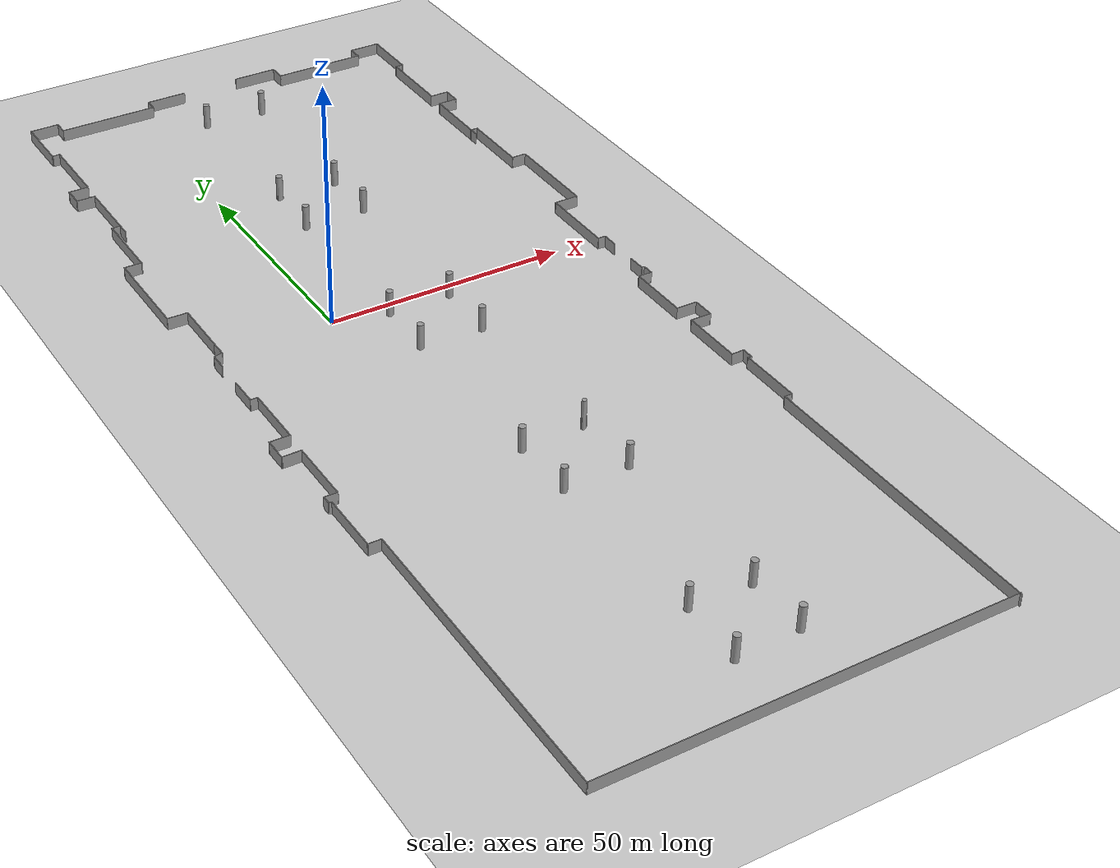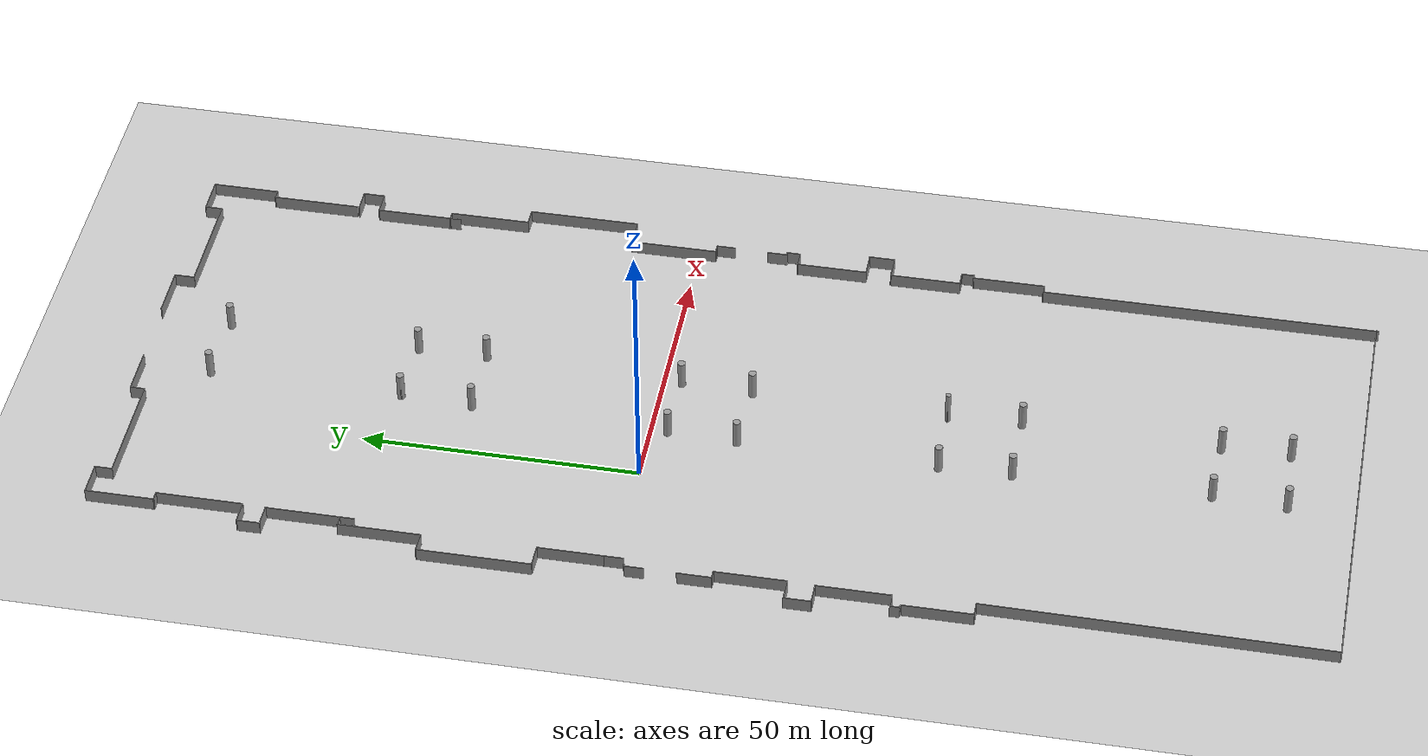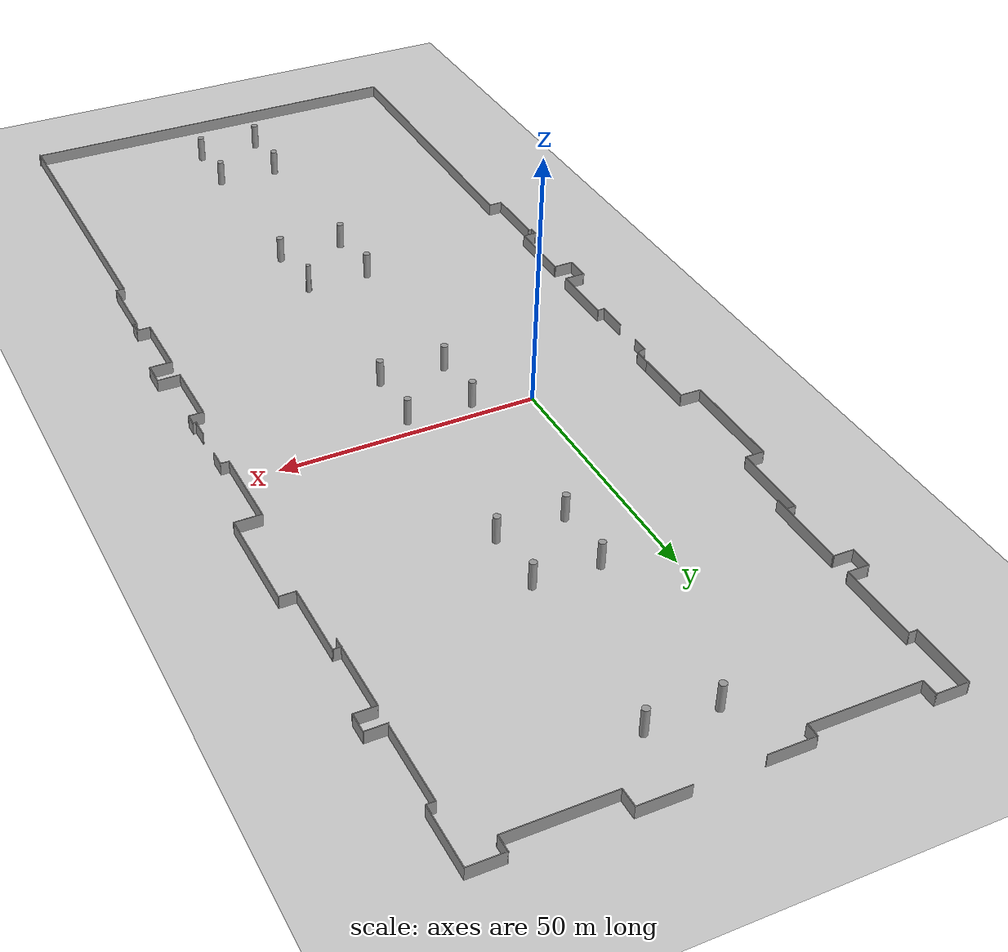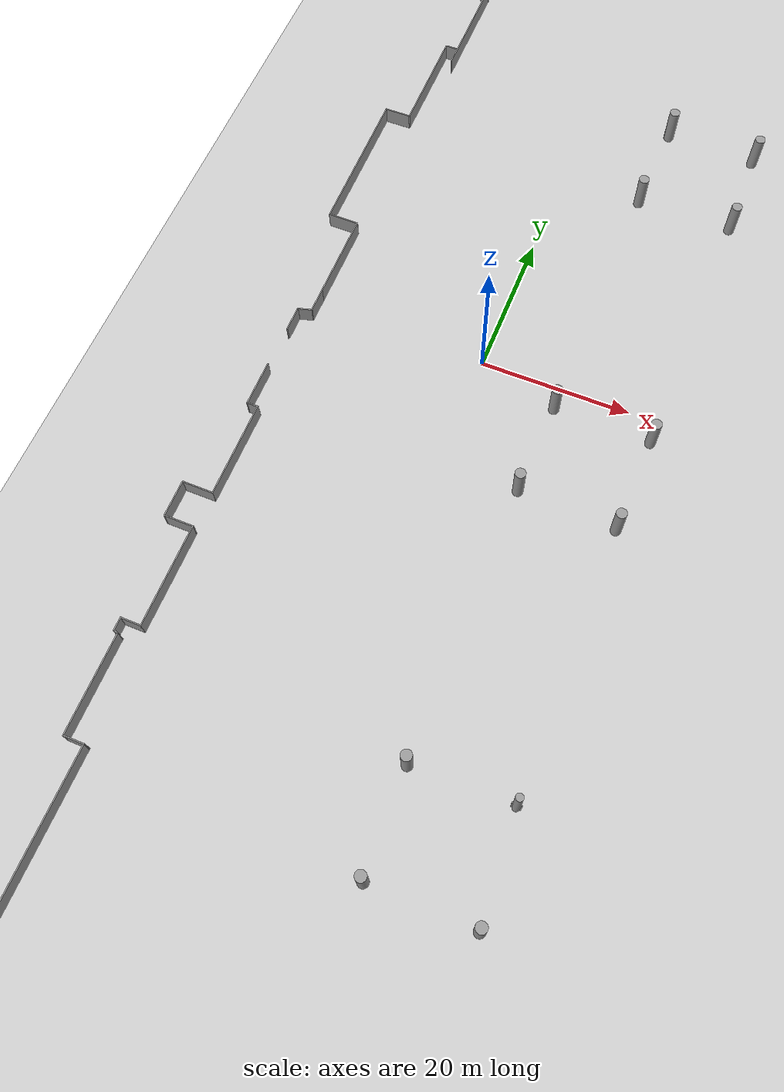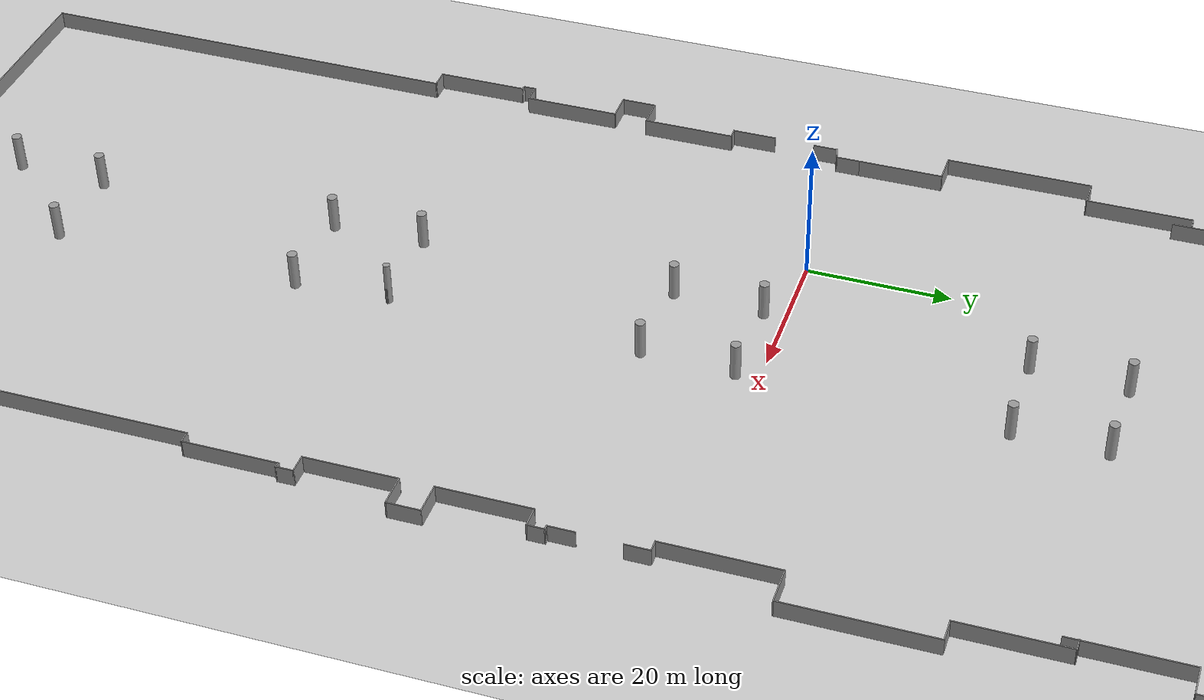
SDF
<sdf version="1.6">
 <world name="default">
  <physics name="default_physics" default="0" type="ode">
   <ode>
    <solver>
     <type>quick</type>
     <iters>20</iters>
     <sor>1</sor>
     <use_dynamic_moi_rescaling>0</use_dynamic_moi_rescaling>
    </solver>
    <constraints>
     <cfm>0</cfm>
     <erp>0.2</erp>
     <contact_max_correcting_vel>100</contact_max_correcting_vel>
     <contact_surface_layer>0</contact_surface_layer>
    </constraints>
   </ode>
   <real_time_update_rate>1000</real_time_update_rate>
   <max_step_size>0.001</max_step_size>
   <real_time_factor>1</real_time_factor>
   <max_contacts>20</max_contacts>
  </physics>
  <light name="sun" type="directional">
   <pose>0 0 10 0 -0 0</pose>
   <diffuse>0.8 0.8 0.8 1</diffuse>
   <specular>0.2 0.2 0.2 1</specular>
   <attenuation>
    <range>1000</range>
    <constant>0.9</constant>
    <linear>0.01</linear>
    <quadratic>0.001</quadratic>
   </attenuation>
   <direction>0.5 0.1 -0.9</direction>
  </light>
  <model name="ground_plane">
   <static>1</static>
   <link name="link">
    <collision name="collision">
     <geometry><plane><normal>0 0 1</normal><size>100 100</size></plane></geometry>
     <surface><friction><ode><mu>100</mu><mu2>50</mu2></ode></friction></surface>
    </collision>
    <visual name="visual">
     <cast_shadows>0</cast_shadows>
     <geometry><plane><normal>0 0 1</normal><size>100 100</size></plane></geometry>
     <material>
      <script><uri>file://media/materials/scripts/gazebo.material</uri><name>Gazebo/Grey</name></script>
     </material>
    </visual>
    <velocity_decay><linear>0</linear><angular>0</angular></velocity_decay>
   </link>
  </model>
  <scene><ambient>0.2 0.2 0.2 1</ambient><background>0.7 0.7 0.7 1</background><shadows>1</shadows></scene>
  <gravity>0 0 -9.81</gravity>
  <magnetic_field>6e-06 2.3e-05 -4.2e-05</magnetic_field>
  <atmosphere type="adiabatic"/>
  <spherical_coordinates>
   <surface_model>EARTH_WGS84</surface_model>
   <latitude_deg>0</latitude_deg>
   <longitude_deg>0</longitude_deg>
   <elevation>0</elevation>
   <heading_deg>0</heading_deg>
  </spherical_coordinates>
  <model name="fira_barcelona_hall_4_space">
   <pose>17.5633 -15.8525 0 0 -0 0</pose>
   <link name="Wall_0">
    <collision name="Wall_0_Collision">
     <geometry><box><size>1.75 0.15 2.5</size></box></geometry>
     <pose>0 0 1.25 0 -0 0</pose>
    </collision>
    <visual name="Wall_0_Visual">
     <pose>0 0 1.25 0 -0 0</pose>
     <geometry><box><size>1.75 0.15 2.5</size></box></geometry>
     <material>
      <script><uri>file://media/materials/scripts/gazebo.material</uri><name>Gazebo/Grey</name></script>
      <ambient>1 1 1 1</ambient>
     </material>
     <meta><layer>0</layer></meta>
    </visual>
    <pose>-40.318 97.4491 0 0 -0 3.14159</pose>
   </link>
   <link name="Wall_1">
    <collision name="Wall_1_Collision">
     <geometry><box><size>12.5 0.15 2.5</size></box></geometry>
     <pose>0 0 1.25 0 -0 0</pose>
    </collision>
    <visual name="Wall_1_Visual">
     <pose>0 0 1.25 0 -0 0</pose>
     <geometry><box><size>12.5 0.15 2.5</size></box></geometry>
     <material>
      <script><uri>file://media/materials/scripts/gazebo.material</uri><name>Gazebo/Grey</name></script>
      <ambient>1 1 1 1</ambient>
     </material>
     <meta><layer>0</layer></meta>
    </visual>
    <pose>-41.118 103.624 0 0 -0 1.5708</pose>
   </link>
   <link name="Wall_101">
    <collision name="Wall_101_Collision">
     <geometry><box><size>0.5 0.15 2.5</size></box></geometry>
     <pose>0 0 1.25 0 -0 0</pose>
    </collision>
    <visual name="Wall_101_Visual">
     <pose>0 0 1.25 0 -0 0</pose>
     <geometry><box><size>0.5 0.15 2.5</size></box></geometry>
     <material>
      <script><uri>file://media/materials/scripts/gazebo.material</uri><name>Gazebo/Grey</name></script>
      <ambient>1 1 1 1</ambient>
     </material>
     <meta><layer>0</layer></meta>
    </visual>
    <pose>-6.12181 61.4561 0 0 -0 0</pose>
   </link>
   <link name="Wall_103">
    <collision name="Wall_103_Collision">
     <geometry><box><size>0.5 0.15 2.5</size></box></geometry>
     <pose>0 0 1.25 0 -0 0</pose>
    </collision>
    <visual name="Wall_103_Visual">
     <pose>0 0 1.25 0 -0 0</pose>
     <geometry><box><size>0.5 0.15 2.5</size></box></geometry>
     <material>
      <script><uri>file://media/materials/scripts/gazebo.material</uri><name>Gazebo/Grey</name></script>
      <ambient>1 1 1 1</ambient>
     </material>
     <meta><layer>0</layer></meta>
    </visual>
    <pose>6.83223 61.2812 0 0 -0 0</pose>
   </link>
   <link name="Wall_105">
    <collision name="Wall_105_Collision">
     <geometry><box><size>0.75 0.15 2.5</size></box></geometry>
     <pose>0 0 1.25 0 -0 0</pose>
    </collision>
    <visual name="Wall_105_Visual">
     <pose>0 0 1.25 0 -0 0</pose>
     <geometry><box><size>0.75 0.15 2.5</size></box></geometry>
     <material>
      <script><uri>file://media/materials/scripts/gazebo.material</uri><name>Gazebo/Grey</name></script>
      <ambient>1 1 1 1</ambient>
     </material>
     <meta><layer>0</layer></meta>
    </visual>
    <pose>-6.18457 48.5681 0 0 -0 0</pose>
   </link>
   <link name="Wall_107">
    <collision name="Wall_107_Collision">
     <geometry><box><size>0.75 0.15 2.5</size></box></geometry>
     <pose>0 0 1.25 0 -0 0</pose>
    </collision>
    <visual name="Wall_107_Visual">
     <pose>0 0 1.25 0 -0 0</pose>
     <geometry><box><size>0.75 0.15 2.5</size></box></geometry>
     <material>
      <script><uri>file://media/materials/scripts/gazebo.material</uri><name>Gazebo/Grey</name></script>
      <ambient>1 1 1 1</ambient>
     </material>
     <meta><layer>0</layer></meta>
    </visual>
    <pose>6.689 48.5074 0 0 -0 0</pose>
   </link>
   <link name="Wall_109">
    <collision name="Wall_109_Collision">
     <geometry><box><size>1 0.15 2.5</size></box></geometry>
     <pose>0 0 1.25 0 -0 0</pose>
    </collision>
    <visual name="Wall_109_Visual">
     <pose>0 0 1.25 0 -0 0</pose>
     <geometry><box><size>1 0.15 2.5</size></box></geometry>
     <material>
      <script><uri>file://media/materials/scripts/gazebo.material</uri><name>Gazebo/Grey</name></script>
      <ambient>1 1 1 1</ambient>
     </material>
     <meta><layer>0</layer></meta>
    </visual>
    <pose>-6.64884 12.973 0 0 -0 0</pose>
   </link>
   <link name="Wall_11">
    <collision name="Wall_11_Collision">
     <geometry><box><size>9.5 0.15 2.5</size></box></geometry>
     <pose>0 0 1.25 0 -0 0</pose>
    </collision>
    <visual name="Wall_11_Visual">
     <pose>0 0 1.25 0 -0 0</pose>
     <geometry><box><size>9.5 0.15 2.5</size></box></geometry>
     <material>
      <script><uri>file://media/materials/scripts/gazebo.material</uri><name>Gazebo/Grey</name></script>
      <ambient>1 1 1 1</ambient>
     </material>
     <meta><layer>0</layer></meta>
    </visual>
    <pose>11.8231 109.582 0 0 -0 0</pose>
   </link>
   <link name="Wall_111">
    <collision name="Wall_111_Collision">
     <geometry><box><size>1.25 0.15 2.5</size></box></geometry>
     <pose>0 0 1.25 0 -0 0</pose>
    </collision>
    <visual name="Wall_111_Visual">
     <pose>0 0 1.25 0 -0 0</pose>
     <geometry><box><size>1.25 0.15 2.5</size></box></geometry>
     <material>
      <script><uri>file://media/materials/scripts/gazebo.material</uri><name>Gazebo/Grey</name></script>
      <ambient>1 1 1 1</ambient>
     </material>
     <meta><layer>0</layer></meta>
    </visual>
    <pose>6.21896 12.7514 0 0 -0 0</pose>
   </link>
   <link name="Wall_113">
    <collision name="Wall_113_Collision">
     <geometry><box><size>1 0.15 2.5</size></box></geometry>
     <pose>0 0 1.25 0 -0 0</pose>
    </collision>
    <visual name="Wall_113_Visual">
     <pose>0 0 1.25 0 -0 0</pose>
     <geometry><box><size>1 0.15 2.5</size></box></geometry>
     <material>
      <script><uri>file://media/materials/scripts/gazebo.material</uri><name>Gazebo/Grey</name></script>
      <ambient>1 1 1 1</ambient>
     </material>
     <meta><layer>0</layer></meta>
    </visual>
    <pose>-7.12748 0.189393 0 0 -0 0</pose>
   </link>
   <link name="Wall_115">
    <collision name="Wall_115_Collision">
     <geometry><box><size>1 0.15 2.5</size></box></geometry>
     <pose>0 0 1.25 0 -0 0</pose>
    </collision>
    <visual name="Wall_115_Visual">
     <pose>0 0 1.25 0 -0 0</pose>
     <geometry><box><size>1 0.15 2.5</size></box></geometry>
     <material>
      <script><uri>file://media/materials/scripts/gazebo.material</uri><name>Gazebo/Grey</name></script>
      <ambient>1 1 1 1</ambient>
     </material>
     <meta><layer>0</layer></meta>
    </visual>
    <pose>5.78394 -0.13821 0 0 -0 0</pose>
   </link>
   <link name="Wall_117">
    <collision name="Wall_117_Collision">
     <geometry><box><size>0.75 0.15 2.5</size></box></geometry>
     <pose>0 0 1.25 0 -0 0</pose>
    </collision>
    <visual name="Wall_117_Visual">
     <pose>0 0 1.25 0 -0 0</pose>
     <geometry><box><size>0.75 0.15 2.5</size></box></geometry>
     <material>
      <script><uri>file://media/materials/scripts/gazebo.material</uri><name>Gazebo/Grey</name></script>
      <ambient>1 1 1 1</ambient>
     </material>
     <meta><layer>0</layer></meta>
    </visual>
    <pose>-7.28351 -35.9394 0 0 -0 0</pose>
   </link>
   <link name="Wall_119">
    <collision name="Wall_119_Collision">
     <geometry><box><size>1.25 0.15 2.5</size></box></geometry>
     <pose>0 0 1.25 0 -0 0</pose>
    </collision>
    <visual name="Wall_119_Visual">
     <pose>0 0 1.25 0 -0 0</pose>
     <geometry><box><size>1.25 0.15 2.5</size></box></geometry>
     <material>
      <script><uri>file://media/materials/scripts/gazebo.material</uri><name>Gazebo/Grey</name></script>
      <ambient>1 1 1 1</ambient>
     </material>
     <meta><layer>0</layer></meta>
    </visual>
    <pose>5.55726 -35.7619 0 0 -0 0</pose>
   </link>
   <link name="Wall_12">
    <collision name="Wall_12_Collision">
     <geometry><box><size>3.75 0.15 2.5</size></box></geometry>
     <pose>0 0 1.25 0 -0 0</pose>
    </collision>
    <visual name="Wall_12_Visual">
     <pose>0 0 1.25 0 -0 0</pose>
     <geometry><box><size>3.75 0.15 2.5</size></box></geometry>
     <material>
      <script><uri>file://media/materials/scripts/gazebo.material</uri><name>Gazebo/Grey</name></script>
      <ambient>1 1 1 1</ambient>
     </material>
     <meta><layer>0</layer></meta>
    </visual>
    <pose>16.4981 107.782 0 0 0 -1.5708</pose>
   </link>
   <link name="Wall_122">
    <collision name="Wall_122_Collision">
     <geometry><box><size>0.75 0.15 2.5</size></box></geometry>
     <pose>0 0 1.25 0 -0 0</pose>
    </collision>
    <visual name="Wall_122_Visual">
     <pose>0 0 1.25 0 -0 0</pose>
     <geometry><box><size>0.75 0.15 2.5</size></box></geometry>
     <material>
      <script><uri>file://media/materials/scripts/gazebo.material</uri><name>Gazebo/Grey</name></script>
      <ambient>1 1 1 1</ambient>
     </material>
     <meta><layer>0</layer></meta>
    </visual>
    <pose>6.20505 -48.7453 0 0 -0 3.14159</pose>
   </link>
   <link name="Wall_124">
    <collision name="Wall_124_Collision">
     <geometry><box><size>0.75 0.15 2.5</size></box></geometry>
     <pose>0 0 1.25 0 -0 0</pose>
    </collision>
    <visual name="Wall_124_Visual">
     <pose>0 0 1.25 0 -0 0</pose>
     <geometry><box><size>0.75 0.15 2.5</size></box></geometry>
     <material>
      <script><uri>file://media/materials/scripts/gazebo.material</uri><name>Gazebo/Grey</name></script>
      <ambient>1 1 1 1</ambient>
     </material>
     <meta><layer>0</layer></meta>
    </visual>
    <pose>-6.89986 -48.7635 0 0 -0 0</pose>
   </link>
   <link name="Wall_126">
    <collision name="Wall_126_Collision">
     <geometry><box><size>0.5 0.15 2.5</size></box></geometry>
     <pose>0 0 1.25 0 -0 0</pose>
    </collision>
    <visual name="Wall_126_Visual">
     <pose>0 0 1.25 0 -0 0</pose>
     <geometry><box><size>0.5 0.15 2.5</size></box></geometry>
     <material>
      <script><uri>file://media/materials/scripts/gazebo.material</uri><name>Gazebo/Grey</name></script>
      <ambient>1 1 1 1</ambient>
     </material>
     <meta><layer>0</layer></meta>
    </visual>
    <pose>-6.30813 -84.3706 0 0 -0 3.14159</pose>
   </link>
   <link name="Wall_128">
    <collision name="Wall_128_Collision">
     <geometry><box><size>0.5 0.15 2.5</size></box></geometry>
     <pose>0 0 1.25 0 -0 0</pose>
    </collision>
    <visual name="Wall_128_Visual">
     <pose>0 0 1.25 0 -0 0</pose>
     <geometry><box><size>0.5 0.15 2.5</size></box></geometry>
     <material>
      <script><uri>file://media/materials/scripts/gazebo.material</uri><name>Gazebo/Grey</name></script>
      <ambient>1 1 1 1</ambient>
     </material>
     <meta><layer>0</layer></meta>
    </visual>
    <pose>6.31753 -84.3242 0 0 -0 0</pose>
   </link>
   <link name="Wall_13">
    <collision name="Wall_13_Collision">
     <geometry><box><size>19.75 0.15 2.5</size></box></geometry>
     <pose>0 0 1.25 0 -0 0</pose>
    </collision>
    <visual name="Wall_13_Visual">
     <pose>0 0 1.25 0 -0 0</pose>
     <geometry><box><size>19.75 0.15 2.5</size></box></geometry>
     <material>
      <script><uri>file://media/materials/scripts/gazebo.material</uri><name>Gazebo/Grey</name></script>
      <ambient>1 1 1 1</ambient>
     </material>
     <meta><layer>0</layer></meta>
    </visual>
    <pose>26.2981 105.982 0 0 -0 0</pose>
   </link>
   <link name="Wall_130">
    <collision name="Wall_130_Collision">
     <geometry><box><size>0.75 0.15 2.5</size></box></geometry>
     <pose>0 0 1.25 0 -0 0</pose>
    </collision>
    <visual name="Wall_130_Visual">
     <pose>0 0 1.25 0 -0 0</pose>
     <geometry><box><size>0.75 0.15 2.5</size></box></geometry>
     <material>
      <script><uri>file://media/materials/scripts/gazebo.material</uri><name>Gazebo/Grey</name></script>
      <ambient>1 1 1 1</ambient>
     </material>
     <meta><layer>0</layer></meta>
    </visual>
    <pose>6.39743 -96.9344 0 0 -0 0</pose>
   </link>
   <link name="Wall_132">
    <collision name="Wall_132_Collision">
     <geometry><box><size>0.5 0.15 2.5</size></box></geometry>
     <pose>0 0 1.25 0 -0 0</pose>
    </collision>
    <visual name="Wall_132_Visual">
     <pose>0 0 1.25 0 -0 0</pose>
     <geometry><box><size>0.5 0.15 2.5</size></box></geometry>
     <material>
      <script><uri>file://media/materials/scripts/gazebo.material</uri><name>Gazebo/Grey</name></script>
      <ambient>1 1 1 1</ambient>
     </material>
     <meta><layer>0</layer></meta>
    </visual>
    <pose>-6.45778 -97.001 0 0 -0 0</pose>
   </link>
   <link name="Wall_14">
    <collision name="Wall_14_Collision">
     <geometry><box><size>3.25 0.15 2.5</size></box></geometry>
     <pose>0 0 1.25 0 -0 0</pose>
    </collision>
    <visual name="Wall_14_Visual">
     <pose>0 0 1.25 0 -0 0</pose>
     <geometry><box><size>3.25 0.15 2.5</size></box></geometry>
     <material>
      <script><uri>file://media/materials/scripts/gazebo.material</uri><name>Gazebo/Grey</name></script>
      <ambient>1 1 1 1</ambient>
     </material>
     <meta><layer>0</layer></meta>
    </visual>
    <pose>36.0981 107.532 0 0 -0 1.5708</pose>
   </link>
   <link name="Wall_15">
    <collision name="Wall_15_Collision">
     <geometry><box><size>6.75 0.15 2.5</size></box></geometry>
     <pose>0 0 1.25 0 -0 0</pose>
    </collision>
    <visual name="Wall_15_Visual">
     <pose>0 0 1.25 0 -0 0</pose>
     <geometry><box><size>6.75 0.15 2.5</size></box></geometry>
     <material>
      <script><uri>file://media/materials/scripts/gazebo.material</uri><name>Gazebo/Grey</name></script>
      <ambient>1 1 1 1</ambient>
     </material>
     <meta><layer>0</layer></meta>
    </visual>
    <pose>39.3981 109.082 0 0 -0 0</pose>
   </link>
   <link name="Wall_16">
    <collision name="Wall_16_Collision">
     <geometry><box><size>12.25 0.15 2.5</size></box></geometry>
     <pose>0 0 1.25 0 -0 0</pose>
    </collision>
    <visual name="Wall_16_Visual">
     <pose>0 0 1.25 0 -0 0</pose>
     <geometry><box><size>12.25 0.15 2.5</size></box></geometry>
     <material>
      <script><uri>file://media/materials/scripts/gazebo.material</uri><name>Gazebo/Grey</name></script>
      <ambient>1 1 1 1</ambient>
     </material>
     <meta><layer>0</layer></meta>
    </visual>
    <pose>42.6981 103.032 0 0 0 -1.5708</pose>
   </link>
   <link name="Wall_19">
    <collision name="Wall_19_Collision">
     <geometry><box><size>1.75 0.15 2.5</size></box></geometry>
     <pose>0 0 1.25 0 -0 0</pose>
    </collision>
    <visual name="Wall_19_Visual">
     <pose>0 0 1.25 0 -0 0</pose>
     <geometry><box><size>1.75 0.15 2.5</size></box></geometry>
     <material>
      <script><uri>file://media/materials/scripts/gazebo.material</uri><name>Gazebo/Grey</name></script>
      <ambient>1 1 1 1</ambient>
     </material>
     <meta><layer>0</layer></meta>
    </visual>
    <pose>41.8981 96.9822 0 0 -0 3.14159</pose>
   </link>
   <link name="Wall_2">
    <collision name="Wall_2_Collision">
     <geometry><box><size>6.25 0.15 2.5</size></box></geometry>
     <pose>0 0 1.25 0 -0 0</pose>
    </collision>
    <visual name="Wall_2_Visual">
     <pose>0 0 1.25 0 -0 0</pose>
     <geometry><box><size>6.25 0.15 2.5</size></box></geometry>
     <material>
      <script><uri>file://media/materials/scripts/gazebo.material</uri><name>Gazebo/Grey</name></script>
      <ambient>1 1 1 1</ambient>
     </material>
     <meta><layer>0</layer></meta>
    </visual>
    <pose>-38.068 109.799 0 0 -0 0</pose>
   </link>
   <link name="Wall_21">
    <collision name="Wall_21_Collision">
     <geometry><box><size>16 0.15 2.5</size></box></geometry>
     <pose>0 0 1.25 0 -0 0</pose>
    </collision>
    <visual name="Wall_21_Visual">
     <pose>0 0 1.25 0 -0 0</pose>
     <geometry><box><size>16 0.15 2.5</size></box></geometry>
     <material>
      <script><uri>file://media/materials/scripts/gazebo.material</uri><name>Gazebo/Grey</name></script>
      <ambient>1 1 1 1</ambient>
     </material>
     <meta><layer>0</layer></meta>
    </visual>
    <pose>41.0981 89.0572 0 0 0 -1.5708</pose>
   </link>
   <link name="Wall_23">
    <collision name="Wall_23_Collision">
     <geometry><box><size>4.25 0.15 2.5</size></box></geometry>
     <pose>0 0 1.25 0 -0 0</pose>
    </collision>
    <visual name="Wall_23_Visual">
     <pose>0 0 1.25 0 -0 0</pose>
     <geometry><box><size>4.25 0.15 2.5</size></box></geometry>
     <material>
      <script><uri>file://media/materials/scripts/gazebo.material</uri><name>Gazebo/Grey</name></script>
      <ambient>1 1 1 1</ambient>
     </material>
     <meta><layer>0</layer></meta>
    </visual>
    <pose>42.9499 80.7475 0 0 -0 0</pose>
   </link>
   <link name="Wall_24">
    <collision name="Wall_24_Collision">
     <geometry><box><size>4 0.15 2.5</size></box></geometry>
     <pose>0 0 1.25 0 -0 0</pose>
    </collision>
    <visual name="Wall_24_Visual">
     <pose>0 0 1.25 0 -0 0</pose>
     <geometry><box><size>4 0.15 2.5</size></box></geometry>
     <material>
      <script><uri>file://media/materials/scripts/gazebo.material</uri><name>Gazebo/Grey</name></script>
      <ambient>1 1 1 1</ambient>
     </material>
     <meta><layer>0</layer></meta>
    </visual>
    <pose>44.9999 78.8225 0 0 0 -1.5708</pose>
   </link>
   <link name="Wall_25">
    <collision name="Wall_25_Collision">
     <geometry><box><size>4.25 0.15 2.5</size></box></geometry>
     <pose>0 0 1.25 0 -0 0</pose>
    </collision>
    <visual name="Wall_25_Visual">
     <pose>0 0 1.25 0 -0 0</pose>
     <geometry><box><size>4.25 0.15 2.5</size></box></geometry>
     <material>
      <script><uri>file://media/materials/scripts/gazebo.material</uri><name>Gazebo/Grey</name></script>
      <ambient>1 1 1 1</ambient>
     </material>
     <meta><layer>0</layer></meta>
    </visual>
    <pose>42.9499 76.8975 0 0 -0 3.14159</pose>
   </link>
   <link name="Wall_27">
    <collision name="Wall_27_Collision">
     <geometry><box><size>15.75 0.15 2.5</size></box></geometry>
     <pose>0 0 1.25 0 -0 0</pose>
    </collision>
    <visual name="Wall_27_Visual">
     <pose>0 0 1.25 0 -0 0</pose>
     <geometry><box><size>15.75 0.15 2.5</size></box></geometry>
     <material>
      <script><uri>file://media/materials/scripts/gazebo.material</uri><name>Gazebo/Grey</name></script>
      <ambient>1 1 1 1</ambient>
     </material>
     <meta><layer>0</layer></meta>
    </visual>
    <pose>40.8999 69.0975 0 0 0 -1.5708</pose>
   </link>
   <link name="Wall_29">
    <collision name="Wall_29_Collision">
     <geometry><box><size>1.70425 0.15 2.5</size></box></geometry>
     <pose>0 0 1.25 0 -0 0</pose>
    </collision>
    <visual name="Wall_29_Visual">
     <pose>0 0 1.25 0 -0 0</pose>
     <geometry><box><size>1.70425 0.15 2.5</size></box></geometry>
     <material>
      <script><uri>file://media/materials/scripts/gazebo.material</uri><name>Gazebo/Grey</name></script>
      <ambient>1 1 1 1</ambient>
     </material>
     <meta><layer>0</layer></meta>
    </visual>
    <pose>41.5884 63.2396 0 0 -0 0.004207</pose>
   </link>
   <link name="Wall_3">
    <collision name="Wall_3_Collision">
     <geometry><box><size>3.25 0.15 2.5</size></box></geometry>
     <pose>0 0 1.25 0 -0 0</pose>
    </collision>
    <visual name="Wall_3_Visual">
     <pose>0 0 1.25 0 -0 0</pose>
     <geometry><box><size>3.25 0.15 2.5</size></box></geometry>
     <material>
      <script><uri>file://media/materials/scripts/gazebo.material</uri><name>Gazebo/Grey</name></script>
      <ambient>1 1 1 1</ambient>
     </material>
     <meta><layer>0</layer></meta>
    </visual>
    <pose>-35.018 108.249 0 0 0 -1.5708</pose>
   </link>
   <link name="Wall_30">
    <collision name="Wall_30_Collision">
     <geometry><box><size>14.75 0.15 2.5</size></box></geometry>
     <pose>0 0 1.25 0 -0 0</pose>
    </collision>
    <visual name="Wall_30_Visual">
     <pose>0 0 1.25 0 -0 0</pose>
     <geometry><box><size>14.75 0.15 2.5</size></box></geometry>
     <material>
      <script><uri>file://media/materials/scripts/gazebo.material</uri><name>Gazebo/Grey</name></script>
      <ambient>1 1 1 1</ambient>
     </material>
     <meta><layer>0</layer></meta>
    </visual>
    <pose>42.3655 55.9428 0 0 0 -1.5708</pose>
   </link>
   <link name="Wall_33">
    <collision name="Wall_33_Collision">
     <geometry><box><size>3.25 0.15 2.5</size></box></geometry>
     <pose>0 0 1.25 0 -0 0</pose>
    </collision>
    <visual name="Wall_33_Visual">
     <pose>0 0 1.25 0 -0 0</pose>
     <geometry><box><size>3.25 0.15 2.5</size></box></geometry>
     <material>
      <script><uri>file://media/materials/scripts/gazebo.material</uri><name>Gazebo/Grey</name></script>
      <ambient>1 1 1 1</ambient>
     </material>
     <meta><layer>0</layer></meta>
    </visual>
    <pose>43.9155 48.6428 0 0 -0 0</pose>
   </link>
   <link name="Wall_34">
    <collision name="Wall_34_Collision">
     <geometry><box><size>20.25 0.15 2.5</size></box></geometry>
     <pose>0 0 1.25 0 -0 0</pose>
    </collision>
    <visual name="Wall_34_Visual">
     <pose>0 0 1.25 0 -0 0</pose>
     <geometry><box><size>20.25 0.15 2.5</size></box></geometry>
     <material>
      <script><uri>file://media/materials/scripts/gazebo.material</uri><name>Gazebo/Grey</name></script>
      <ambient>1 1 1 1</ambient>
     </material>
     <meta><layer>0</layer></meta>
    </visual>
    <pose>45.4655 38.5928 0 0 0 -1.5708</pose>
   </link>
   <link name="Wall_36">
    <collision name="Wall_36_Collision">
     <geometry><box><size>15.75 0.15 2.5</size></box></geometry>
     <pose>0 0 1.25 0 -0 0</pose>
    </collision>
    <visual name="Wall_36_Visual">
     <pose>0 0 1.25 0 -0 0</pose>
     <geometry><box><size>15.75 0.15 2.5</size></box></geometry>
     <material>
      <script><uri>file://media/materials/scripts/gazebo.material</uri><name>Gazebo/Grey</name></script>
      <ambient>1 1 1 1</ambient>
     </material>
     <meta><layer>0</layer></meta>
    </visual>
    <pose>-39.518 89.6491 0 0 0 -1.5708</pose>
   </link>
   <link name="Wall_37">
    <collision name="Wall_37_Collision">
     <geometry><box><size>4.25 0.15 2.5</size></box></geometry>
     <pose>0 0 1.25 0 -0 0</pose>
    </collision>
    <visual name="Wall_37_Visual">
     <pose>0 0 1.25 0 -0 0</pose>
     <geometry><box><size>4.25 0.15 2.5</size></box></geometry>
     <material>
      <script><uri>file://media/materials/scripts/gazebo.material</uri><name>Gazebo/Grey</name></script>
      <ambient>1 1 1 1</ambient>
     </material>
     <meta><layer>0</layer></meta>
    </visual>
    <pose>-41.568 81.8491 0 0 -0 3.14159</pose>
   </link>
   <link name="Wall_38">
    <collision name="Wall_38_Collision">
     <geometry><box><size>4.25 0.15 2.5</size></box></geometry>
     <pose>0 0 1.25 0 -0 0</pose>
    </collision>
    <visual name="Wall_38_Visual">
     <pose>0 0 1.25 0 -0 0</pose>
     <geometry><box><size>4.25 0.15 2.5</size></box></geometry>
     <material>
      <script><uri>file://media/materials/scripts/gazebo.material</uri><name>Gazebo/Grey</name></script>
      <ambient>1 1 1 1</ambient>
     </material>
     <meta><layer>0</layer></meta>
    </visual>
    <pose>-43.618 79.7991 0 0 0 -1.5708</pose>
   </link>
   <link name="Wall_39">
    <collision name="Wall_39_Collision">
     <geometry><box><size>4.08128 0.15 2.5</size></box></geometry>
     <pose>0 0 1.25 0 -0 0</pose>
    </collision>
    <visual name="Wall_39_Visual">
     <pose>0 0 1.25 0 -0 0</pose>
     <geometry><box><size>4.08128 0.15 2.5</size></box></geometry>
     <material>
      <script><uri>file://media/materials/scripts/gazebo.material</uri><name>Gazebo/Grey</name></script>
      <ambient>1 1 1 1</ambient>
     </material>
     <meta><layer>0</layer></meta>
    </visual>
    <pose>-41.6528 77.7089 0 0 0 -0.020467</pose>
   </link>
   <link name="Wall_40">
    <collision name="Wall_40_Collision">
     <geometry><box><size>16 0.15 2.5</size></box></geometry>
     <pose>0 0 1.25 0 -0 0</pose>
    </collision>
    <visual name="Wall_40_Visual">
     <pose>0 0 1.25 0 -0 0</pose>
     <geometry><box><size>16 0.15 2.5</size></box></geometry>
     <material>
      <script><uri>file://media/materials/scripts/gazebo.material</uri><name>Gazebo/Grey</name></script>
      <ambient>1 1 1 1</ambient>
     </material>
     <meta><layer>0</layer></meta>
    </visual>
    <pose>-39.7278 69.7839 0 0 0 -1.5708</pose>
   </link>
   <link name="Wall_42">
    <collision name="Wall_42_Collision">
     <geometry><box><size>1.75 0.15 2.5</size></box></geometry>
     <pose>0 0 1.25 0 -0 0</pose>
    </collision>
    <visual name="Wall_42_Visual">
     <pose>0 0 1.25 0 -0 0</pose>
     <geometry><box><size>1.75 0.15 2.5</size></box></geometry>
     <material>
      <script><uri>file://media/materials/scripts/gazebo.material</uri><name>Gazebo/Grey</name></script>
      <ambient>1 1 1 1</ambient>
     </material>
     <meta><layer>0</layer></meta>
    </visual>
    <pose>-40.7188 64.3851 0 0 -0 3.14159</pose>
   </link>
   <link name="Wall_43">
    <collision name="Wall_43_Collision">
     <geometry><box><size>14.9402 0.15 2.5</size></box></geometry>
     <pose>0 0 1.25 0 -0 0</pose>
    </collision>
    <visual name="Wall_43_Visual">
     <pose>0 0 1.25 0 -0 0</pose>
     <geometry><box><size>14.9402 0.15 2.5</size></box></geometry>
     <material>
      <script><uri>file://media/materials/scripts/gazebo.material</uri><name>Gazebo/Grey</name></script>
      <ambient>1 1 1 1</ambient>
     </material>
     <meta><layer>0</layer></meta>
    </visual>
    <pose>-41.5226 56.99 0 0 0 -1.5713</pose>
   </link>
   <link name="Wall_45">
    <collision name="Wall_45_Collision">
     <geometry><box><size>3.75 0.15 2.5</size></box></geometry>
     <pose>0 0 1.25 0 -0 0</pose>
    </collision>
    <visual name="Wall_45_Visual">
     <pose>0 0 1.25 0 -0 0</pose>
     <geometry><box><size>3.75 0.15 2.5</size></box></geometry>
     <material>
      <script><uri>file://media/materials/scripts/gazebo.material</uri><name>Gazebo/Grey</name></script>
      <ambient>1 1 1 1</ambient>
     </material>
     <meta><layer>0</layer></meta>
    </visual>
    <pose>-43.3263 49.6098 0 0 -0 3.14159</pose>
   </link>
   <link name="Wall_46">
    <collision name="Wall_46_Collision">
     <geometry><box><size>20.5 0.15 2.5</size></box></geometry>
     <pose>0 0 1.25 0 -0 0</pose>
    </collision>
    <visual name="Wall_46_Visual">
     <pose>0 0 1.25 0 -0 0</pose>
     <geometry><box><size>20.5 0.15 2.5</size></box></geometry>
     <material>
      <script><uri>file://media/materials/scripts/gazebo.material</uri><name>Gazebo/Grey</name></script>
      <ambient>1 1 1 1</ambient>
     </material>
     <meta><layer>0</layer></meta>
    </visual>
    <pose>-45.1263 39.4348 0 0 0 -1.5708</pose>
   </link>
   <link name="Wall_48">
    <collision name="Wall_48_Collision">
     <geometry><box><size>5.25 0.15 2.5</size></box></geometry>
     <pose>0 0 1.25 0 -0 0</pose>
    </collision>
    <visual name="Wall_48_Visual">
     <pose>0 0 1.25 0 -0 0</pose>
     <geometry><box><size>5.25 0.15 2.5</size></box></geometry>
     <material>
      <script><uri>file://media/materials/scripts/gazebo.material</uri><name>Gazebo/Grey</name></script>
      <ambient>1 1 1 1</ambient>
     </material>
     <meta><layer>0</layer></meta>
    </visual>
    <pose>42.9155 28.5428 0 0 -0 3.14159</pose>
   </link>
   <link name="Wall_49">
    <collision name="Wall_49_Collision">
     <geometry><box><size>16 0.15 2.5</size></box></geometry>
     <pose>0 0 1.25 0 -0 0</pose>
    </collision>
    <visual name="Wall_49_Visual">
     <pose>0 0 1.25 0 -0 0</pose>
     <geometry><box><size>16 0.15 2.5</size></box></geometry>
     <material>
      <script><uri>file://media/materials/scripts/gazebo.material</uri><name>Gazebo/Grey</name></script>
      <ambient>1 1 1 1</ambient>
     </material>
     <meta><layer>0</layer></meta>
    </visual>
    <pose>40.3655 20.6178 0 0 0 -1.5708</pose>
   </link>
   <link name="Wall_51">
    <collision name="Wall_51_Collision">
     <geometry><box><size>1.73908 0.15 2.5</size></box></geometry>
     <pose>0 0 1.25 0 -0 0</pose>
    </collision>
    <visual name="Wall_51_Visual">
     <pose>0 0 1.25 0 -0 0</pose>
     <geometry><box><size>1.73908 0.15 2.5</size></box></geometry>
     <material>
      <script><uri>file://media/materials/scripts/gazebo.material</uri><name>Gazebo/Grey</name></script>
      <ambient>1 1 1 1</ambient>
     </material>
     <meta><layer>0</layer></meta>
    </visual>
    <pose>41.1601 12.6874 0 0 0 -0.006895</pose>
   </link>
   <link name="Wall_52">
    <collision name="Wall_52_Collision">
     <geometry><box><size>3.5 0.15 2.5</size></box></geometry>
     <pose>0 0 1.25 0 -0 0</pose>
    </collision>
    <visual name="Wall_52_Visual">
     <pose>0 0 1.25 0 -0 0</pose>
     <geometry><box><size>3.5 0.15 2.5</size></box></geometry>
     <material>
      <script><uri>file://media/materials/scripts/gazebo.material</uri><name>Gazebo/Grey</name></script>
      <ambient>1 1 1 1</ambient>
     </material>
     <meta><layer>0</layer></meta>
    </visual>
    <pose>41.9655 10.9959 0 0 0 -1.5708</pose>
   </link>
   <link name="Wall_54">
    <collision name="Wall_54_Collision">
     <geometry><box><size>3.75 0.15 2.5</size></box></geometry>
     <pose>0 0 1.25 0 -0 0</pose>
    </collision>
    <visual name="Wall_54_Visual">
     <pose>0 0 1.25 0 -0 0</pose>
     <geometry><box><size>3.75 0.15 2.5</size></box></geometry>
     <material>
      <script><uri>file://media/materials/scripts/gazebo.material</uri><name>Gazebo/Grey</name></script>
      <ambient>1 1 1 1</ambient>
     </material>
     <meta><layer>0</layer></meta>
    </visual>
    <pose>41.7942 1.36232 0 0 0 -1.5708</pose>
   </link>
   <link name="Wall_55">
    <collision name="Wall_55_Collision">
     <geometry><box><size>0.75 0.15 2.5</size></box></geometry>
     <pose>0 0 1.25 0 -0 0</pose>
    </collision>
    <visual name="Wall_55_Visual">
     <pose>0 0 1.25 0 -0 0</pose>
     <geometry><box><size>0.75 0.15 2.5</size></box></geometry>
     <material>
      <script><uri>file://media/materials/scripts/gazebo.material</uri><name>Gazebo/Grey</name></script>
      <ambient>1 1 1 1</ambient>
     </material>
     <meta><layer>0</layer></meta>
    </visual>
    <pose>42.0942 -0.437681 0 0 -0 0</pose>
   </link>
   <link name="Wall_56">
    <collision name="Wall_56_Collision">
     <geometry><box><size>2.5 0.15 2.5</size></box></geometry>
     <pose>0 0 1.25 0 -0 0</pose>
    </collision>
    <visual name="Wall_56_Visual">
     <pose>0 0 1.25 0 -0 0</pose>
     <geometry><box><size>2.5 0.15 2.5</size></box></geometry>
     <material>
      <script><uri>file://media/materials/scripts/gazebo.material</uri><name>Gazebo/Grey</name></script>
      <ambient>1 1 1 1</ambient>
     </material>
     <meta><layer>0</layer></meta>
    </visual>
    <pose>42.3942 -1.61268 0 0 0 -1.5708</pose>
   </link>
   <link name="Wall_57">
    <collision name="Wall_57_Collision">
     <geometry><box><size>3 0.15 2.5</size></box></geometry>
     <pose>0 0 1.25 0 -0 0</pose>
    </collision>
    <visual name="Wall_57_Visual">
     <pose>0 0 1.25 0 -0 0</pose>
     <geometry><box><size>3 0.15 2.5</size></box></geometry>
     <material>
      <script><uri>file://media/materials/scripts/gazebo.material</uri><name>Gazebo/Grey</name></script>
      <ambient>1 1 1 1</ambient>
     </material>
     <meta><layer>0</layer></meta>
    </visual>
    <pose>40.9692 -2.78768 0 0 -0 3.14159</pose>
   </link>
   <link name="Wall_59">
    <collision name="Wall_59_Collision">
     <geometry><box><size>13 0.15 2.5</size></box></geometry>
     <pose>0 0 1.25 0 -0 0</pose>
    </collision>
    <visual name="Wall_59_Visual">
     <pose>0 0 1.25 0 -0 0</pose>
     <geometry><box><size>13 0.15 2.5</size></box></geometry>
     <material>
      <script><uri>file://media/materials/scripts/gazebo.material</uri><name>Gazebo/Grey</name></script>
      <ambient>1 1 1 1</ambient>
     </material>
     <meta><layer>0</layer></meta>
    </visual>
    <pose>39.5442 -9.21268 0 0 0 -1.5708</pose>
   </link>
   <link name="Wall_61">
    <collision name="Wall_61_Collision">
     <geometry><box><size>4.5 0.15 2.5</size></box></geometry>
     <pose>0 0 1.25 0 -0 0</pose>
    </collision>
    <visual name="Wall_61_Visual">
     <pose>0 0 1.25 0 -0 0</pose>
     <geometry><box><size>4.5 0.15 2.5</size></box></geometry>
     <material>
      <script><uri>file://media/materials/scripts/gazebo.material</uri><name>Gazebo/Grey</name></script>
      <ambient>1 1 1 1</ambient>
     </material>
     <meta><layer>0</layer></meta>
    </visual>
    <pose>41.7192 -15.6377 0 0 -0 0</pose>
   </link>
   <link name="Wall_62">
    <collision name="Wall_62_Collision">
     <geometry><box><size>4.75 0.15 2.5</size></box></geometry>
     <pose>0 0 1.25 0 -0 0</pose>
    </collision>
    <visual name="Wall_62_Visual">
     <pose>0 0 1.25 0 -0 0</pose>
     <geometry><box><size>4.75 0.15 2.5</size></box></geometry>
     <material>
      <script><uri>file://media/materials/scripts/gazebo.material</uri><name>Gazebo/Grey</name></script>
      <ambient>1 1 1 1</ambient>
     </material>
     <meta><layer>0</layer></meta>
    </visual>
    <pose>43.8942 -17.9377 0 0 0 -1.5708</pose>
   </link>
   <link name="Wall_63">
    <collision name="Wall_63_Collision">
     <geometry><box><size>4.5 0.15 2.5</size></box></geometry>
     <pose>0 0 1.25 0 -0 0</pose>
    </collision>
    <visual name="Wall_63_Visual">
     <pose>0 0 1.25 0 -0 0</pose>
     <geometry><box><size>4.5 0.15 2.5</size></box></geometry>
     <material>
      <script><uri>file://media/materials/scripts/gazebo.material</uri><name>Gazebo/Grey</name></script>
      <ambient>1 1 1 1</ambient>
     </material>
     <meta><layer>0</layer></meta>
    </visual>
    <pose>41.7192 -20.2377 0 0 -0 3.14159</pose>
   </link>
   <link name="Wall_64">
    <collision name="Wall_64_Collision">
     <geometry><box><size>13 0.15 2.5</size></box></geometry>
     <pose>0 0 1.25 0 -0 0</pose>
    </collision>
    <visual name="Wall_64_Visual">
     <pose>0 0 1.25 0 -0 0</pose>
     <geometry><box><size>13 0.15 2.5</size></box></geometry>
     <material>
      <script><uri>file://media/materials/scripts/gazebo.material</uri><name>Gazebo/Grey</name></script>
      <ambient>1 1 1 1</ambient>
     </material>
     <meta><layer>0</layer></meta>
    </visual>
    <pose>39.5442 -26.6627 0 0 0 -1.5708</pose>
   </link>
   <link name="Wall_65">
    <collision name="Wall_65_Collision">
     <geometry><box><size>2.75 0.15 2.5</size></box></geometry>
     <pose>0 0 1.25 0 -0 0</pose>
    </collision>
    <visual name="Wall_65_Visual">
     <pose>0 0 1.25 0 -0 0</pose>
     <geometry><box><size>2.75 0.15 2.5</size></box></geometry>
     <material>
      <script><uri>file://media/materials/scripts/gazebo.material</uri><name>Gazebo/Grey</name></script>
      <ambient>1 1 1 1</ambient>
     </material>
     <meta><layer>0</layer></meta>
    </visual>
    <pose>40.8442 -33.0877 0 0 -0 0</pose>
   </link>
   <link name="Wall_66">
    <collision name="Wall_66_Collision">
     <geometry><box><size>2.5 0.15 2.5</size></box></geometry>
     <pose>0 0 1.25 0 -0 0</pose>
    </collision>
    <visual name="Wall_66_Visual">
     <pose>0 0 1.25 0 -0 0</pose>
     <geometry><box><size>2.5 0.15 2.5</size></box></geometry>
     <material>
      <script><uri>file://media/materials/scripts/gazebo.material</uri><name>Gazebo/Grey</name></script>
      <ambient>1 1 1 1</ambient>
     </material>
     <meta><layer>0</layer></meta>
    </visual>
    <pose>42.1442 -34.2627 0 0 0 -1.5708</pose>
   </link>
   <link name="Wall_67">
    <collision name="Wall_67_Collision">
     <geometry><box><size>0.832842 0.15 2.5</size></box></geometry>
     <pose>0 0 1.25 0 -0 0</pose>
    </collision>
    <visual name="Wall_67_Visual">
     <pose>0 0 1.25 0 -0 0</pose>
     <geometry><box><size>0.832842 0.15 2.5</size></box></geometry>
     <material>
      <script><uri>file://media/materials/scripts/gazebo.material</uri><name>Gazebo/Grey</name></script>
      <ambient>1 1 1 1</ambient>
     </material>
     <meta><layer>0</layer></meta>
    </visual>
    <pose>41.8056 -35.3934 0 0 -0 3.01148</pose>
   </link>
   <link name="Wall_68">
    <collision name="Wall_68_Collision">
     <geometry><box><size>13.25 0.15 2.5</size></box></geometry>
     <pose>0 0 1.25 0 -0 0</pose>
    </collision>
    <visual name="Wall_68_Visual">
     <pose>0 0 1.25 0 -0 0</pose>
     <geometry><box><size>13.25 0.15 2.5</size></box></geometry>
     <material>
      <script><uri>file://media/materials/scripts/gazebo.material</uri><name>Gazebo/Grey</name></script>
      <ambient>1 1 1 1</ambient>
     </material>
     <meta><layer>0</layer></meta>
    </visual>
    <pose>41.4671 -41.8991 0 0 0 -1.5708</pose>
   </link>
   <link name="Wall_69">
    <collision name="Wall_69_Collision">
     <geometry><box><size>1.75 0.15 2.5</size></box></geometry>
     <pose>0 0 1.25 0 -0 0</pose>
    </collision>
    <visual name="Wall_69_Visual">
     <pose>0 0 1.25 0 -0 0</pose>
     <geometry><box><size>1.75 0.15 2.5</size></box></geometry>
     <material>
      <script><uri>file://media/materials/scripts/gazebo.material</uri><name>Gazebo/Grey</name></script>
      <ambient>1 1 1 1</ambient>
     </material>
     <meta><layer>0</layer></meta>
    </visual>
    <pose>40.6671 -48.4491 0 0 -0 3.14159</pose>
   </link>
   <link name="Wall_7">
    <collision name="Wall_7_Collision">
     <geometry><box><size>21 0.15 2.5</size></box></geometry>
     <pose>0 0 1.25 0 -0 0</pose>
    </collision>
    <visual name="Wall_7_Visual">
     <pose>0 0 1.25 0 -0 0</pose>
     <geometry><box><size>21 0.15 2.5</size></box></geometry>
     <material>
      <script><uri>file://media/materials/scripts/gazebo.material</uri><name>Gazebo/Grey</name></script>
      <ambient>1 1 1 1</ambient>
     </material>
     <meta><layer>0</layer></meta>
    </visual>
    <pose>-24.593 106.699 0 0 -0 0</pose>
   </link>
   <link name="Wall_70">
    <collision name="Wall_70_Collision">
     <geometry><box><size>61.5 0.15 2.5</size></box></geometry>
     <pose>0 0 1.25 0 -0 0</pose>
    </collision>
    <visual name="Wall_70_Visual">
     <pose>0 0 1.25 0 -0 0</pose>
     <geometry><box><size>61.5 0.15 2.5</size></box></geometry>
     <material>
      <script><uri>file://media/materials/scripts/gazebo.material</uri><name>Gazebo/Grey</name></script>
      <ambient>1 1 1 1</ambient>
     </material>
     <meta><layer>0</layer></meta>
    </visual>
    <pose>39.8671 -79.1241 0 0 0 -1.5708</pose>
   </link>
   <link name="Wall_72">
    <collision name="Wall_72_Collision">
     <geometry><box><size>81.75 0.15 2.5</size></box></geometry>
     <pose>0 0 1.25 0 -0 0</pose>
    </collision>
    <visual name="Wall_72_Visual">
     <pose>0 0 1.25 0 -0 0</pose>
     <geometry><box><size>81.75 0.15 2.5</size></box></geometry>
     <material>
      <script><uri>file://media/materials/scripts/gazebo.material</uri><name>Gazebo/Grey</name></script>
      <ambient>1 1 1 1</ambient>
     </material>
     <meta><layer>0</layer></meta>
    </visual>
    <pose>-0.747011 -109.399 0 0 -0 3.14159</pose>
   </link>
   <link name="Wall_73">
    <collision name="Wall_73_Collision">
     <geometry><box><size>62.252 0.15 2.5</size></box></geometry>
     <pose>0 0 1.25 0 -0 0</pose>
    </collision>
    <visual name="Wall_73_Visual">
     <pose>0 0 1.25 0 -0 0</pose>
     <geometry><box><size>62.252 0.15 2.5</size></box></geometry>
     <material>
      <script><uri>file://media/materials/scripts/gazebo.material</uri><name>Gazebo/Grey</name></script>
      <ambient>1 1 1 1</ambient>
     </material>
     <meta><layer>0</layer></meta>
    </visual>
    <pose>-41.297 -78.3493 0 0 -0 1.56275</pose>
   </link>
   <link name="Wall_74">
    <collision name="Wall_74_Collision">
     <geometry><box><size>2.75 0.15 2.5</size></box></geometry>
     <pose>0 0 1.25 0 -0 0</pose>
    </collision>
    <visual name="Wall_74_Visual">
     <pose>0 0 1.25 0 -0 0</pose>
     <geometry><box><size>2.75 0.15 2.5</size></box></geometry>
     <material>
      <script><uri>file://media/materials/scripts/gazebo.material</uri><name>Gazebo/Grey</name></script>
      <ambient>1 1 1 1</ambient>
     </material>
     <meta><layer>0</layer></meta>
    </visual>
    <pose>-42.347 -47.2993 0 0 -0 3.14159</pose>
   </link>
   <link name="Wall_77">
    <collision name="Wall_77_Collision">
     <geometry><box><size>12.75 0.15 2.5</size></box></geometry>
     <pose>0 0 1.25 0 -0 0</pose>
    </collision>
    <visual name="Wall_77_Visual">
     <pose>0 0 1.25 0 -0 0</pose>
     <geometry><box><size>12.75 0.15 2.5</size></box></geometry>
     <material>
      <script><uri>file://media/materials/scripts/gazebo.material</uri><name>Gazebo/Grey</name></script>
      <ambient>1 1 1 1</ambient>
     </material>
     <meta><layer>0</layer></meta>
    </visual>
    <pose>-43.647 -40.9993 0 0 -0 1.5708</pose>
   </link>
   <link name="Wall_78">
    <collision name="Wall_78_Collision">
     <geometry><box><size>0.75 0.15 2.5</size></box></geometry>
     <pose>0 0 1.25 0 -0 0</pose>
    </collision>
    <visual name="Wall_78_Visual">
     <pose>0 0 1.25 0 -0 0</pose>
     <geometry><box><size>0.75 0.15 2.5</size></box></geometry>
     <material>
      <script><uri>file://media/materials/scripts/gazebo.material</uri><name>Gazebo/Grey</name></script>
      <ambient>1 1 1 1</ambient>
     </material>
     <meta><layer>0</layer></meta>
    </visual>
    <pose>-43.9368 -34.6217 0 0 -0 2.87979</pose>
   </link>
   <link name="Wall_79">
    <collision name="Wall_79_Collision">
     <geometry><box><size>1.79497 0.15 2.5</size></box></geometry>
     <pose>0 0 1.25 0 -0 0</pose>
    </collision>
    <visual name="Wall_79_Visual">
     <pose>0 0 1.25 0 -0 0</pose>
     <geometry><box><size>1.79497 0.15 2.5</size></box></geometry>
     <material>
      <script><uri>file://media/materials/scripts/gazebo.material</uri><name>Gazebo/Grey</name></script>
      <ambient>1 1 1 1</ambient>
     </material>
     <meta><layer>0</layer></meta>
    </visual>
    <pose>-44.2266 -33.7216 0 0 -0 1.5708</pose>
   </link>
   <link name="Wall_8">
    <collision name="Wall_8_Collision">
     <geometry><box><size>2.75 0.15 2.5</size></box></geometry>
     <pose>0 0 1.25 0 -0 0</pose>
    </collision>
    <visual name="Wall_8_Visual">
     <pose>0 0 1.25 0 -0 0</pose>
     <geometry><box><size>2.75 0.15 2.5</size></box></geometry>
     <material>
      <script><uri>file://media/materials/scripts/gazebo.material</uri><name>Gazebo/Grey</name></script>
      <ambient>1 1 1 1</ambient>
     </material>
     <meta><layer>0</layer></meta>
    </visual>
    <pose>-14.168 107.999 0 0 -0 1.5708</pose>
   </link>
   <link name="Wall_80">
    <collision name="Wall_80_Collision">
     <geometry><box><size>2.75 0.15 2.5</size></box></geometry>
     <pose>0 0 1.25 0 -0 0</pose>
    </collision>
    <visual name="Wall_80_Visual">
     <pose>0 0 1.25 0 -0 0</pose>
     <geometry><box><size>2.75 0.15 2.5</size></box></geometry>
     <material>
      <script><uri>file://media/materials/scripts/gazebo.material</uri><name>Gazebo/Grey</name></script>
      <ambient>1 1 1 1</ambient>
     </material>
     <meta><layer>0</layer></meta>
    </visual>
    <pose>-42.9153 -32.9103 0 0 -0 0</pose>
   </link>
   <link name="Wall_82">
    <collision name="Wall_82_Collision">
     <geometry><box><size>13.5 0.15 2.5</size></box></geometry>
     <pose>0 0 1.25 0 -0 0</pose>
    </collision>
    <visual name="Wall_82_Visual">
     <pose>0 0 1.25 0 -0 0</pose>
     <geometry><box><size>13.5 0.15 2.5</size></box></geometry>
     <material>
      <script><uri>file://media/materials/scripts/gazebo.material</uri><name>Gazebo/Grey</name></script>
      <ambient>1 1 1 1</ambient>
     </material>
     <meta><layer>0</layer></meta>
    </visual>
    <pose>-41.6153 -26.2353 0 0 -0 1.5708</pose>
   </link>
   <link name="Wall_83">
    <collision name="Wall_83_Collision">
     <geometry><box><size>4 0.15 2.5</size></box></geometry>
     <pose>0 0 1.25 0 -0 0</pose>
    </collision>
    <visual name="Wall_83_Visual">
     <pose>0 0 1.25 0 -0 0</pose>
     <geometry><box><size>4 0.15 2.5</size></box></geometry>
     <material>
      <script><uri>file://media/materials/scripts/gazebo.material</uri><name>Gazebo/Grey</name></script>
      <ambient>1 1 1 1</ambient>
     </material>
     <meta><layer>0</layer></meta>
    </visual>
    <pose>-43.5403 -19.5603 0 0 -0 3.14159</pose>
   </link>
   <link name="Wall_84">
    <collision name="Wall_84_Collision">
     <geometry><box><size>5 0.15 2.5</size></box></geometry>
     <pose>0 0 1.25 0 -0 0</pose>
    </collision>
    <visual name="Wall_84_Visual">
     <pose>0 0 1.25 0 -0 0</pose>
     <geometry><box><size>5 0.15 2.5</size></box></geometry>
     <material>
      <script><uri>file://media/materials/scripts/gazebo.material</uri><name>Gazebo/Grey</name></script>
      <ambient>1 1 1 1</ambient>
     </material>
     <meta><layer>0</layer></meta>
    </visual>
    <pose>-45.4653 -17.1353 0 0 -0 1.5708</pose>
   </link>
   <link name="Wall_85">
    <collision name="Wall_85_Collision">
     <geometry><box><size>4.21629 0.15 2.5</size></box></geometry>
     <pose>0 0 1.25 0 -0 0</pose>
    </collision>
    <visual name="Wall_85_Visual">
     <pose>0 0 1.25 0 -0 0</pose>
     <geometry><box><size>4.21629 0.15 2.5</size></box></geometry>
     <material>
      <script><uri>file://media/materials/scripts/gazebo.material</uri><name>Gazebo/Grey</name></script>
      <ambient>1 1 1 1</ambient>
     </material>
     <meta><layer>0</layer></meta>
    </visual>
    <pose>-43.4322 -14.7159 0 0 0 -0.002765</pose>
   </link>
   <link name="Wall_86">
    <collision name="Wall_86_Collision">
     <geometry><box><size>13 0.15 2.5</size></box></geometry>
     <pose>0 0 1.25 0 -0 0</pose>
    </collision>
    <visual name="Wall_86_Visual">
     <pose>0 0 1.25 0 -0 0</pose>
     <geometry><box><size>13 0.15 2.5</size></box></geometry>
     <material>
      <script><uri>file://media/materials/scripts/gazebo.material</uri><name>Gazebo/Grey</name></script>
      <ambient>1 1 1 1</ambient>
     </material>
     <meta><layer>0</layer></meta>
    </visual>
    <pose>-41.3934 -8.29093 0 0 -0 1.5708</pose>
   </link>
   <link name="Wall_88">
    <collision name="Wall_88_Collision">
     <geometry><box><size>1.5 0.15 2.5</size></box></geometry>
     <pose>0 0 1.25 0 -0 0</pose>
    </collision>
    <visual name="Wall_88_Visual">
     <pose>0 0 1.25 0 -0 0</pose>
     <geometry><box><size>1.5 0.15 2.5</size></box></geometry>
     <material>
      <script><uri>file://media/materials/scripts/gazebo.material</uri><name>Gazebo/Grey</name></script>
      <ambient>1 1 1 1</ambient>
     </material>
     <meta><layer>0</layer></meta>
    </visual>
    <pose>-42.1899 -1.8555 0 0 -0 3.14159</pose>
   </link>
   <link name="Wall_89">
    <collision name="Wall_89_Collision">
     <geometry><box><size>6.25 0.15 2.5</size></box></geometry>
     <pose>0 0 1.25 0 -0 0</pose>
    </collision>
    <visual name="Wall_89_Visual">
     <pose>0 0 1.25 0 -0 0</pose>
     <geometry><box><size>6.25 0.15 2.5</size></box></geometry>
     <material>
      <script><uri>file://media/materials/scripts/gazebo.material</uri><name>Gazebo/Grey</name></script>
      <ambient>1 1 1 1</ambient>
     </material>
     <meta><layer>0</layer></meta>
    </visual>
    <pose>-42.8649 1.1945 0 0 -0 1.5708</pose>
   </link>
   <link name="Wall_9">
    <collision name="Wall_9_Collision">
     <geometry><box><size>8.75 0.15 2.5</size></box></geometry>
     <pose>0 0 1.25 0 -0 0</pose>
    </collision>
    <visual name="Wall_9_Visual">
     <pose>0 0 1.25 0 -0 0</pose>
     <geometry><box><size>8.75 0.15 2.5</size></box></geometry>
     <material>
      <script><uri>file://media/materials/scripts/gazebo.material</uri><name>Gazebo/Grey</name></script>
      <ambient>1 1 1 1</ambient>
     </material>
     <meta><layer>0</layer></meta>
    </visual>
    <pose>-9.86799 109.299 0 0 -0 0</pose>
   </link>
   <link name="Wall_91">
    <collision name="Wall_91_Collision">
     <geometry><box><size>3.5 0.15 2.5</size></box></geometry>
     <pose>0 0 1.25 0 -0 0</pose>
    </collision>
    <visual name="Wall_91_Visual">
     <pose>0 0 1.25 0 -0 0</pose>
     <geometry><box><size>3.5 0.15 2.5</size></box></geometry>
     <material>
      <script><uri>file://media/materials/scripts/gazebo.material</uri><name>Gazebo/Grey</name></script>
      <ambient>1 1 1 1</ambient>
     </material>
     <meta><layer>0</layer></meta>
    </visual>
    <pose>-42.7889 11.7789 0 0 -0 1.5708</pose>
   </link>
   <link name="Wall_92">
    <collision name="Wall_92_Collision">
     <geometry><box><size>2 0.15 2.5</size></box></geometry>
     <pose>0 0 1.25 0 -0 0</pose>
    </collision>
    <visual name="Wall_92_Visual">
     <pose>0 0 1.25 0 -0 0</pose>
     <geometry><box><size>2 0.15 2.5</size></box></geometry>
     <material>
      <script><uri>file://media/materials/scripts/gazebo.material</uri><name>Gazebo/Grey</name></script>
      <ambient>1 1 1 1</ambient>
     </material>
     <meta><layer>0</layer></meta>
    </visual>
    <pose>-41.8954 13.6933 0 0 -0 0.261799</pose>
   </link>
   <link name="Wall_93">
    <collision name="Wall_93_Collision">
     <geometry><box><size>3.51978 0.15 2.5</size></box></geometry>
     <pose>0 0 1.25 0 -0 0</pose>
    </collision>
    <visual name="Wall_93_Visual">
     <pose>0 0 1.25 0 -0 0</pose>
     <geometry><box><size>3.51978 0.15 2.5</size></box></geometry>
     <material>
      <script><uri>file://media/materials/scripts/gazebo.material</uri><name>Gazebo/Grey</name></script>
      <ambient>1 1 1 1</ambient>
     </material>
     <meta><layer>0</layer></meta>
    </visual>
    <pose>-41.0019 15.6176 0 0 -0 1.5708</pose>
   </link>
   <link name="Wall_94">
    <collision name="Wall_94_Collision">
     <geometry><box><size>12 0.15 2.5</size></box></geometry>
     <pose>0 0 1.25 0 -0 0</pose>
    </collision>
    <visual name="Wall_94_Visual">
     <pose>0 0 1.25 0 -0 0</pose>
     <geometry><box><size>12 0.15 2.5</size></box></geometry>
     <material>
      <script><uri>file://media/materials/scripts/gazebo.material</uri><name>Gazebo/Grey</name></script>
      <ambient>1 1 1 1</ambient>
     </material>
     <meta><layer>0</layer></meta>
    </visual>
    <pose>-41.0019 23.2176 0 0 -0 1.5708</pose>
   </link>
   <link name="Wall_95">
    <collision name="Wall_95_Collision">
     <geometry><box><size>4.27007 0.15 2.5</size></box></geometry>
     <pose>0 0 1.25 0 -0 0</pose>
    </collision>
    <visual name="Wall_95_Visual">
     <pose>0 0 1.25 0 -0 0</pose>
     <geometry><box><size>4.27007 0.15 2.5</size></box></geometry>
     <material>
      <script><uri>file://media/materials/scripts/gazebo.material</uri><name>Gazebo/Grey</name></script>
      <ambient>1 1 1 1</ambient>
     </material>
     <meta><layer>0</layer></meta>
    </visual>
    <pose>-43.0618 29.1673 0 0 -0 3.12959</pose>
   </link>
   <link name="Wall_97">
    <collision name="Wall_97_Collision">
     <geometry><box><size>0.25 0.15 2.5</size></box></geometry>
     <pose>0 0 1.25 0 -0 0</pose>
    </collision>
    <visual name="Wall_97_Visual">
     <pose>0 0 1.25 0 -0 0</pose>
     <geometry><box><size>0.25 0.15 2.5</size></box></geometry>
     <material>
      <script><uri>file://media/materials/scripts/gazebo.material</uri><name>Gazebo/Grey</name></script>
      <ambient>1 1 1 1</ambient>
     </material>
     <meta><layer>0</layer></meta>
    </visual>
    <pose>-5.61138 96.9337 0 0 -0 0.261799</pose>
   </link>
   <link name="Wall_99">
    <collision name="Wall_99_Collision">
     <geometry><box><size>0.5 0.15 2.5</size></box></geometry>
     <pose>0 0 1.25 0 -0 0</pose>
    </collision>
    <visual name="Wall_99_Visual">
     <pose>0 0 1.25 0 -0 0</pose>
     <geometry><box><size>0.5 0.15 2.5</size></box></geometry>
     <material>
      <script><uri>file://media/materials/scripts/gazebo.material</uri><name>Gazebo/Grey</name></script>
      <ambient>1 1 1 1</ambient>
     </material>
     <meta><layer>0</layer></meta>
    </visual>
    <pose>7.33763 96.8064 0 0 -0 0</pose>
   </link>
   <static>1</static>
  </model>
  <model name="pillars_set_1_0">
   <pose>23.1233 -51.5766 3.09304 0 -0 0.001488</pose>
   <link name="link">
    <inertial>
     <mass>1</mass>
     <inertia><ixx>0.145833</ixx><ixy>0</ixy><ixz>0</ixz><iyy>0.145833</iyy><iyz>0</iyz><izz>0.125</izz></inertia>
    </inertial>
    <collision name="collision">
     <geometry><cylinder><radius>0.476559</radius><length>6.18608</length></cylinder></geometry>
    </collision>
    <visual name="visual">
     <geometry><cylinder><radius>0.476559</radius><length>6.18608</length></cylinder></geometry>
     <material>
      <script><name>Gazebo/Grey</name><uri>file://media/materials/scripts/gazebo.material</uri></script>
     </material>
    </visual>
   </link>
  </model>
  <model name="pillars_set_1_1">
   <pose>10.328 -51.7591 2.70258 0 -0 0.00074</pose>
   <link name="link">
    <inertial>
     <mass>1</mass>
     <inertia><ixx>0.145833</ixx><ixy>0</ixy><ixz>0</ixz><iyy>0.145833</iyy><iyz>0</iyz><izz>0.125</izz></inertia>
    </inertial>
    <collision name="collision">
     <geometry><cylinder><radius>0.692158</radius><length>5.40516</length></cylinder></geometry>
    </collision>
    <visual name="visual">
     <geometry><cylinder><radius>0.692158</radius><length>5.40516</length></cylinder></geometry>
     <material>
      <script><name>Gazebo/Grey</name><uri>file://media/materials/scripts/gazebo.material</uri></script>
     </material>
    </visual>
   </link>
  </model>
  <model name="pillars_set_1_2">
   <pose>10.5698 -64.8614 2.70258 0 -0 0.00074</pose>
   <link name="link">
    <inertial>
     <mass>1</mass>
     <inertia><ixx>0.145833</ixx><ixy>0</ixy><ixz>0</ixz><iyy>0.145833</iyy><iyz>0</iyz><izz>0.125</izz></inertia>
    </inertial>
    <collision name="collision">
     <geometry><cylinder><radius>0.692158</radius><length>5.40516</length></cylinder></geometry>
    </collision>
    <visual name="visual">
     <geometry><cylinder><radius>0.692158</radius><length>5.40516</length></cylinder></geometry>
     <material>
      <script><name>Gazebo/Grey</name><uri>file://media/materials/scripts/gazebo.material</uri></script>
     </material>
    </visual>
   </link>
  </model>
  <model name="pillars_set_1_3">
   <pose>23.85 -64.9005 2.70258 0 -0 0.00074</pose>
   <link name="link">
    <inertial>
     <mass>1</mass>
     <inertia><ixx>0.145833</ixx><ixy>0</ixy><ixz>0</ixz><iyy>0.145833</iyy><iyz>0</iyz><izz>0.125</izz></inertia>
    </inertial>
    <collision name="collision">
     <geometry><cylinder><radius>0.692158</radius><length>5.40516</length></cylinder></geometry>
    </collision>
    <visual name="visual">
     <geometry><cylinder><radius>0.692158</radius><length>5.40516</length></cylinder></geometry>
     <material>
      <script><name>Gazebo/Grey</name><uri>file://media/materials/scripts/gazebo.material</uri></script>
     </material>
    </visual>
   </link>
  </model>
  <model name="pillars_set_4_0">
   <pose>23.3677 -16.1979 2.70258 0 -0 0.00074</pose>
   <link name="link">
    <inertial>
     <mass>1</mass>
     <inertia><ixx>0.145833</ixx><ixy>0</ixy><ixz>0</ixz><iyy>0.145833</iyy><iyz>0</iyz><izz>0.125</izz></inertia>
    </inertial>
    <collision name="collision">
     <geometry><cylinder><radius>0.692158</radius><length>5.40516</length></cylinder></geometry>
    </collision>
    <visual name="visual">
     <geometry><cylinder><radius>0.692158</radius><length>5.40516</length></cylinder></geometry>
     <material>
      <script><name>Gazebo/Grey</name><uri>file://media/materials/scripts/gazebo.material</uri></script>
     </material>
    </visual>
   </link>
  </model>
  <model name="pillars_set_4_1">
   <pose>10.4745 -15.6418 2.70258 0 -0 0.00074</pose>
   <link name="link">
    <inertial>
     <mass>1</mass>
     <inertia><ixx>0.145833</ixx><ixy>0</ixy><ixz>0</ixz><iyy>0.145833</iyy><iyz>0</iyz><izz>0.125</izz></inertia>
    </inertial>
    <collision name="collision">
     <geometry><cylinder><radius>0.692158</radius><length>5.40516</length></cylinder></geometry>
    </collision>
    <visual name="visual">
     <geometry><cylinder><radius>0.692158</radius><length>5.40516</length></cylinder></geometry>
     <material>
      <script><name>Gazebo/Grey</name><uri>file://media/materials/scripts/gazebo.material</uri></script>
     </material>
    </visual>
   </link>
  </model>
  <model name="pillars_set_4_2">
   <pose>23.8093 -3.21496 2.70258 0 -0 0.00074</pose>
   <link name="link">
    <inertial>
     <mass>1</mass>
     <inertia><ixx>0.145833</ixx><ixy>0</ixy><ixz>0</ixz><iyy>0.145833</iyy><iyz>0</iyz><izz>0.125</izz></inertia>
    </inertial>
    <collision name="collision">
     <geometry><cylinder><radius>0.692158</radius><length>5.40516</length></cylinder></geometry>
    </collision>
    <visual name="visual">
     <geometry><cylinder><radius>0.692158</radius><length>5.40516</length></cylinder></geometry>
     <material>
      <script><name>Gazebo/Grey</name><uri>file://media/materials/scripts/gazebo.material</uri></script>
     </material>
    </visual>
   </link>
  </model>
  <model name="pillars_set_4_3">
   <pose>10.9049 -3.06022 2.70258 0 -0 0.00074</pose>
   <link name="link">
    <inertial>
     <mass>1</mass>
     <inertia><ixx>0.145833</ixx><ixy>0</ixy><ixz>0</ixz><iyy>0.145833</iyy><iyz>0</iyz><izz>0.125</izz></inertia>
    </inertial>
    <collision name="collision">
     <geometry><cylinder><radius>0.692158</radius><length>5.40516</length></cylinder></geometry>
    </collision>
    <visual name="visual">
     <geometry><cylinder><radius>0.692158</radius><length>5.40516</length></cylinder></geometry>
     <material>
      <script><name>Gazebo/Grey</name><uri>file://media/materials/scripts/gazebo.material</uri></script>
     </material>
    </visual>
   </link>
  </model>
  <model name="pillars_set_5_0">
   <pose>24.6853 80.594 2.70258 0 -0 0.00074</pose>
   <link name="link">
    <inertial>
     <mass>1</mass>
     <inertia><ixx>0.145833</ixx><ixy>0</ixy><ixz>0</ixz><iyy>0.145833</iyy><iyz>0</iyz><izz>0.125</izz></inertia>
    </inertial>
    <collision name="collision">
     <geometry><cylinder><radius>0.692158</radius><length>5.40516</length></cylinder></geometry>
    </collision>
    <visual name="visual">
     <geometry><cylinder><radius>0.692158</radius><length>5.40516</length></cylinder></geometry>
     <material>
      <script><name>Gazebo/Grey</name><uri>file://media/materials/scripts/gazebo.material</uri></script>
     </material>
    </visual>
   </link>
  </model>
  <model name="pillars_set_5_1">
   <pose>11.7753 81.025 2.70258 0 -0 0.00074</pose>
   <link name="link">
    <inertial>
     <mass>1</mass>
     <inertia><ixx>0.145833</ixx><ixy>0</ixy><ixz>0</ixz><iyy>0.145833</iyy><iyz>0</iyz><izz>0.125</izz></inertia>
    </inertial>
    <collision name="collision">
     <geometry><cylinder><radius>0.692158</radius><length>5.40516</length></cylinder></geometry>
    </collision>
    <visual name="visual">
     <geometry><cylinder><radius>0.692158</radius><length>5.40516</length></cylinder></geometry>
     <material>
      <script><name>Gazebo/Grey</name><uri>file://media/materials/scripts/gazebo.material</uri></script>
     </material>
    </visual>
   </link>
  </model>
  <model name="pillars_set_2_2">
   <pose>24.3421 45.4161 2.70258 0 -0 0.00074</pose>
   <link name="link">
    <inertial>
     <mass>1</mass>
     <inertia><ixx>0.145833</ixx><ixy>0</ixy><ixz>0</ixz><iyy>0.145833</iyy><iyz>0</iyz><izz>0.125</izz></inertia>
    </inertial>
    <collision name="collision">
     <geometry><cylinder><radius>0.692158</radius><length>5.40516</length></cylinder></geometry>
    </collision>
    <visual name="visual">
     <geometry><cylinder><radius>0.692158</radius><length>5.40516</length></cylinder></geometry>
     <material>
      <script><name>Gazebo/Grey</name><uri>file://media/materials/scripts/gazebo.material</uri></script>
     </material>
    </visual>
   </link>
  </model>
  <model name="pillars_set_2_3">
   <pose>11.869 45.7747 2.70258 0 -0 0.00074</pose>
   <link name="link">
    <inertial>
     <mass>1</mass>
     <inertia><ixx>0.145833</ixx><ixy>0</ixy><ixz>0</ixz><iyy>0.145833</iyy><iyz>0</iyz><izz>0.125</izz></inertia>
    </inertial>
    <collision name="collision">
     <geometry><cylinder><radius>0.692158</radius><length>5.40516</length></cylinder></geometry>
    </collision>
    <visual name="visual">
     <geometry><cylinder><radius>0.692158</radius><length>5.40516</length></cylinder></geometry>
     <material>
      <script><name>Gazebo/Grey</name><uri>file://media/materials/scripts/gazebo.material</uri></script>
     </material>
    </visual>
   </link>
  </model>
  <model name="pillars_set_2_0">
   <pose>11.3048 32.6795 2.70258 0 -0 0.00074</pose>
   <link name="link">
    <inertial>
     <mass>1</mass>
     <inertia><ixx>0.145833</ixx><ixy>0</ixy><ixz>0</ixz><iyy>0.145833</iyy><iyz>0</iyz><izz>0.125</izz></inertia>
    </inertial>
    <collision name="collision">
     <geometry><cylinder><radius>0.692158</radius><length>5.40516</length></cylinder></geometry>
    </collision>
    <visual name="visual">
     <geometry><cylinder><radius>0.692158</radius><length>5.40516</length></cylinder></geometry>
     <material>
      <script><name>Gazebo/Grey</name><uri>file://media/materials/scripts/gazebo.material</uri></script>
     </material>
    </visual>
   </link>
  </model>
  <model name="pillars_set_2_1">
   <pose>24.375 32.7941 2.70258 0 -0 0.00074</pose>
   <link name="link">
    <inertial>
     <mass>1</mass>
     <inertia><ixx>0.145833</ixx><ixy>0</ixy><ixz>0</ixz><iyy>0.145833</iyy><iyz>0</iyz><izz>0.125</izz></inertia>
    </inertial>
    <collision name="collision">
     <geometry><cylinder><radius>0.692158</radius><length>5.40516</length></cylinder></geometry>
    </collision>
    <visual name="visual">
     <geometry><cylinder><radius>0.692158</radius><length>5.40516</length></cylinder></geometry>
     <material>
      <script><name>Gazebo/Grey</name><uri>file://media/materials/scripts/gazebo.material</uri></script>
     </material>
    </visual>
   </link>
  </model>
  <model name="pillars_set_3_0">
   <pose>11.4449 -100.011 2.70258 0 -0 0.00074</pose>
   <link name="link">
    <inertial>
     <mass>1</mass>
     <inertia><ixx>0.145833</ixx><ixy>0</ixy><ixz>0</ixz><iyy>0.145833</iyy><iyz>0</iyz><izz>0.125</izz></inertia>
    </inertial>
    <collision name="collision">
     <geometry><cylinder><radius>0.692158</radius><length>5.40516</length></cylinder></geometry>
    </collision>
    <visual name="visual">
     <geometry><cylinder><radius>0.692158</radius><length>5.40516</length></cylinder></geometry>
     <material>
      <script><name>Gazebo/Grey</name><uri>file://media/materials/scripts/gazebo.material</uri></script>
     </material>
    </visual>
   </link>
  </model>
  <model name="pillars_set_3_2">
   <pose>23.8753 -112.818 2.70258 0 -0 0.00074</pose>
   <link name="link">
    <inertial>
     <mass>1</mass>
     <inertia><ixx>0.145833</ixx><ixy>0</ixy><ixz>0</ixz><iyy>0.145833</iyy><iyz>0</iyz><izz>0.125</izz></inertia>
    </inertial>
    <collision name="collision">
     <geometry><cylinder><radius>0.692158</radius><length>5.40516</length></cylinder></geometry>
    </collision>
    <visual name="visual">
     <geometry><cylinder><radius>0.692158</radius><length>5.40516</length></cylinder></geometry>
     <material>
      <script><name>Gazebo/Grey</name><uri>file://media/materials/scripts/gazebo.material</uri></script>
     </material>
    </visual>
   </link>
  </model>
  <model name="pillars_set_3_1">
   <pose>23.746 -100.443 2.70258 0 -0 0.00074</pose>
   <link name="link">
    <inertial>
     <mass>1</mass>
     <inertia><ixx>0.145833</ixx><ixy>0</ixy><ixz>0</ixz><iyy>0.145833</iyy><iyz>0</iyz><izz>0.125</izz></inertia>
    </inertial>
    <collision name="collision">
     <geometry><cylinder><radius>0.692158</radius><length>5.40516</length></cylinder></geometry>
    </collision>
    <visual name="visual">
     <geometry><cylinder><radius>0.692158</radius><length>5.40516</length></cylinder></geometry>
     <material>
      <script><name>Gazebo/Grey</name><uri>file://media/materials/scripts/gazebo.material</uri></script>
     </material>
    </visual>
   </link>
  </model>
  <model name="pillars_set_3_3">
   <pose>10.8868 -113.263 2.70258 0 -0 0.00074</pose>
   <link name="link">
    <inertial>
     <mass>1</mass>
     <inertia><ixx>0.145833</ixx><ixy>0</ixy><ixz>0</ixz><iyy>0.145833</iyy><iyz>0</iyz><izz>0.125</izz></inertia>
    </inertial>
    <collision name="collision">
     <geometry><cylinder><radius>0.692158</radius><length>5.40516</length></cylinder></geometry>
    </collision>
    <visual name="visual">
     <geometry><cylinder><radius>0.692158</radius><length>5.40516</length></cylinder></geometry>
     <material>
      <script><name>Gazebo/Grey</name><uri>file://media/materials/scripts/gazebo.material</uri></script>
     </material>
    </visual>
   </link>
  </model>
 </world>
</sdf>
